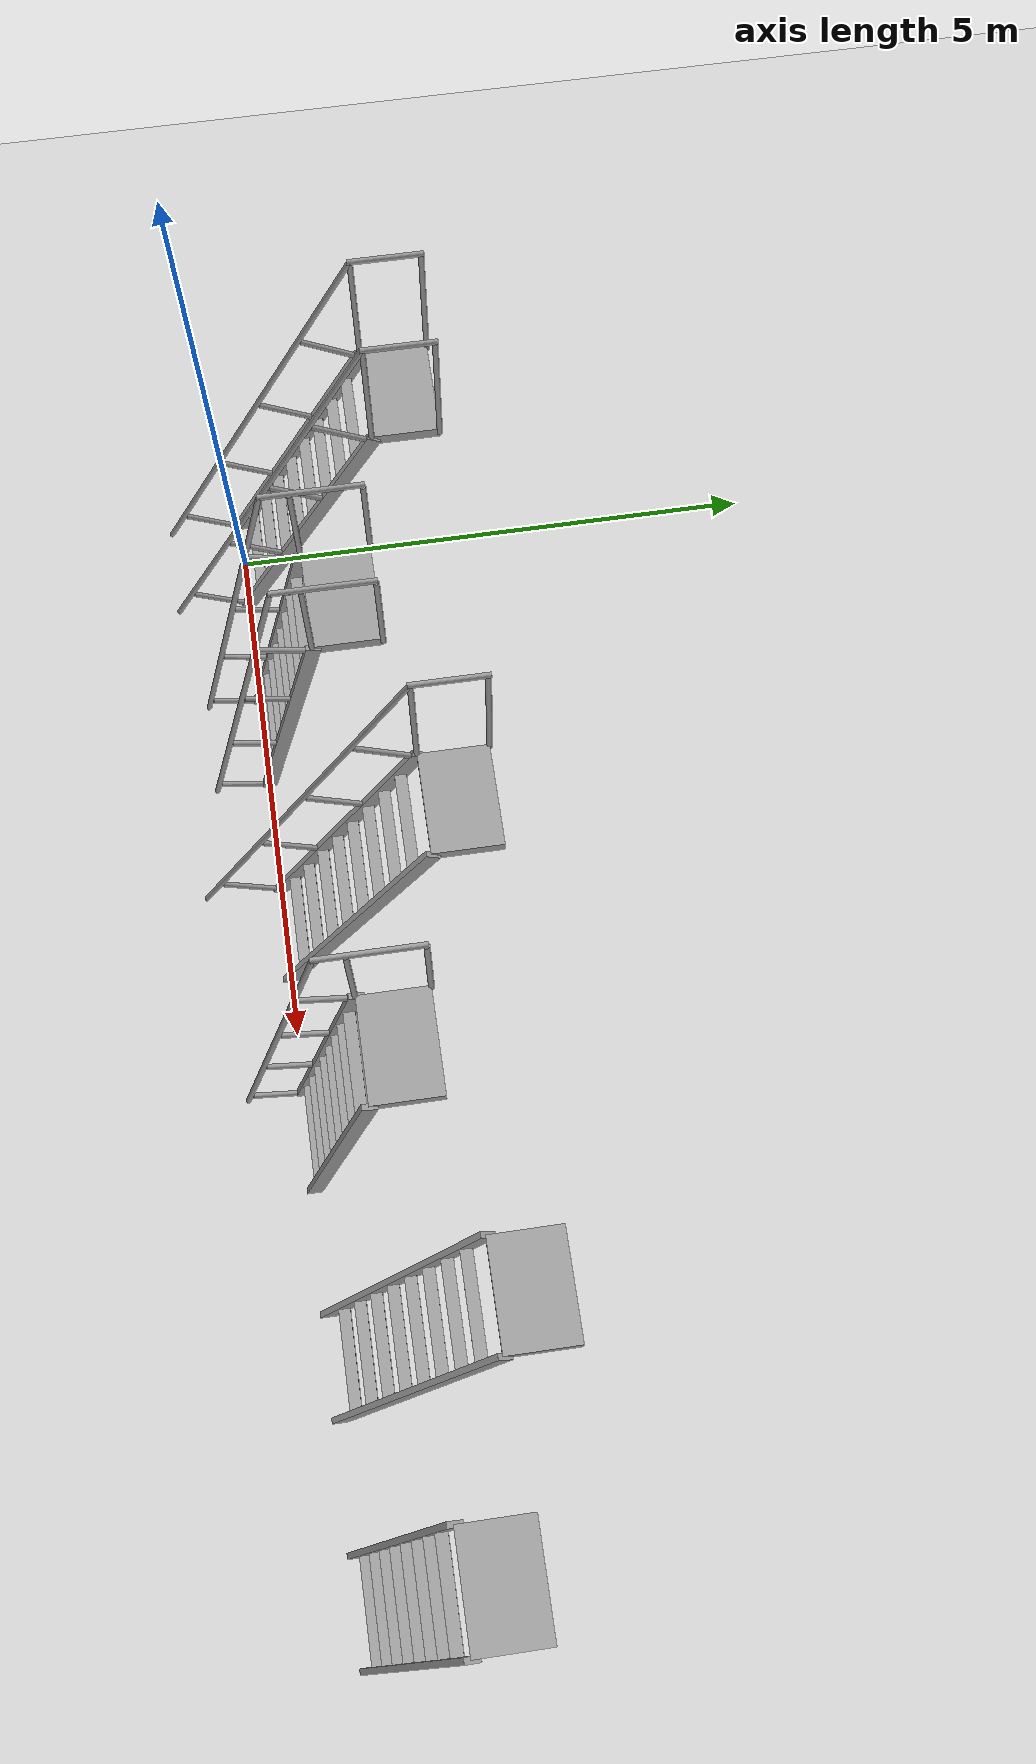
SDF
<?xml version="1.0" ?>
<sdf version="1.4">
  <world name="trials_task_3">
    <physics type="ode">
      <gravity>0 0 -9.81</gravity>
      <ode>
        <solver>
          <type>quick</type>
          <iters>50</iters>
          <sor>1.4</sor>
        </solver>
        <constraints>
          <cfm>0.0</cfm>
          <erp>0.2</erp>
          <contact_max_correcting_vel>100.0</contact_max_correcting_vel>
          <contact_surface_layer>0.0</contact_surface_layer>
        </constraints>
      </ode>
      <real_time_update_rate>1000</real_time_update_rate>
      <max_step_size>0.001</max_step_size>
    </physics>

    <!--A global light source -->
    <include>
      <uri>model://sun</uri>
    </include>

    <!-- A ground plane -->
    <include>
      <uri>model://ground_plane</uri>
    </include>

    <include>
      <name>ladder</name>
      <uri>model://ladder_60deg_2rails</uri>
    </include>

    <include>
      <name>ladder</name>
      <uri>model://ladder_75deg_2rails</uri>
      <pose>2 0 0 0 0 0</pose>
    </include>

    <include>
      <name>ladder</name>
      <uri>model://ladder_60deg_1rails</uri>
      <pose>4 0 0 0 0 0</pose>
    </include>

    <include>
      <name>ladder</name>
      <uri>model://ladder_75deg_1rails</uri>
      <pose>6 0 0 0 0 0</pose>
    </include>

    <include>
      <name>ladder</name>
      <uri>model://ladder_60deg_0rails</uri>
      <pose>8 0 0 0 0 0</pose>
    </include>

    <include>
      <name>ladder</name>
      <uri>model://ladder_75deg_0rails</uri>
      <pose>10 0 0 0 0 0</pose>
    </include>

    <plugin filename="libVRCPlugin.so" name="vrc_plugin">
      <atlas>
        <model_name>atlas</model_name>
        <pin_link>utorso</pin_link>
      </atlas>
      <drc_vehicle>
        <model_name>drc_vehicle_xp900</model_name>
        <seat_link>polaris_ranger_xp900::chassis</seat_link>
      </drc_vehicle>
      <drc_fire_hose>
        <fire_hose_model>fire_hose</fire_hose_model>
        <coupling_link>coupling</coupling_link>
        <standpipe_model>standpipe</standpipe_model>
        <spout_link>standpipe</spout_link>
        <thread_pitch>-1000</thread_pitch>
        <coupling_relative_pose>1.17038e-05 -0.125623 0.35 -0.0412152 -1.57078 1.61199</coupling_relative_pose>
      </drc_fire_hose>
    </plugin>

  </world>
</sdf>

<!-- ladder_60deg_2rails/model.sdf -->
<sdf version="1.5">

  <model name= "ladder_60deg_2rails" >
    <static>true</static>
         <link name="step0" >
           <pose>0 0.15396007178390025 0.26666666666666666 0 0 0 </pose>
           <inertial>
             <mass> 9.7548192</mass>
             <inertia>
             <ixx> 0.009571241631672</ixx>
             <iyy> 0.6596303120915761</iyy>
             <izz> 0.666841521540096</izz>
             <ixy>0</ixy>
             <ixz>0</ixz>
             <iyz>0</iyz>
             </inertia>
           </inertial>

           <collision name="collision">
             <geometry>
              <box>
                <size>  0.9  0.1016  0.0381  </size>
              </box>
             </geometry>
           </collision>

          <visual name="visual">
            <geometry>
              <box>
                <size>  0.9  0.1016  0.0381  </size>
              </box>
            </geometry>
            <material>
              <script>
                <uri>file://media/materials/scripts/gazebo.material</uri>
                <name>Gazebo/Grey</name>
              </script>
            </material>
          </visual>
        </link>
         <link name="step1" >
           <pose>0 0.3079201435678005 0.5333333333333333 0 0 0 </pose>
           <inertial>
             <mass> 9.7548192</mass>
             <inertia>
             <ixx> 0.009571241631672</ixx>
             <iyy> 0.6596303120915761</iyy>
             <izz> 0.666841521540096</izz>
             <ixy>0</ixy>
             <ixz>0</ixz>
             <iyz>0</iyz>
             </inertia>
           </inertial>

           <collision name="collision">
             <geometry>
              <box>
                <size>  0.9  0.1016  0.0381  </size>
              </box>
             </geometry>
           </collision>

          <visual name="visual">
            <geometry>
              <box>
                <size>  0.9  0.1016  0.0381  </size>
              </box>
            </geometry>
            <material>
              <script>
                <uri>file://media/materials/scripts/gazebo.material</uri>
                <name>Gazebo/Grey</name>
              </script>
            </material>
          </visual>
        </link>
         <link name="step2" >
           <pose>0 0.46188021535170076 0.8 0 0 0 </pose>
           <inertial>
             <mass> 9.7548192</mass>
             <inertia>
             <ixx> 0.009571241631672</ixx>
             <iyy> 0.6596303120915761</iyy>
             <izz> 0.666841521540096</izz>
             <ixy>0</ixy>
             <ixz>0</ixz>
             <iyz>0</iyz>
             </inertia>
           </inertial>

           <collision name="collision">
             <geometry>
              <box>
                <size>  0.9  0.1016  0.0381  </size>
              </box>
             </geometry>
           </collision>

          <visual name="visual">
            <geometry>
              <box>
                <size>  0.9  0.1016  0.0381  </size>
              </box>
            </geometry>
            <material>
              <script>
                <uri>file://media/materials/scripts/gazebo.material</uri>
                <name>Gazebo/Grey</name>
              </script>
            </material>
          </visual>
        </link>
         <link name="step3" >
           <pose>0 0.615840287135601 1.0666666666666667 0 0 0 </pose>
           <inertial>
             <mass> 9.7548192</mass>
             <inertia>
             <ixx> 0.009571241631672</ixx>
             <iyy> 0.6596303120915761</iyy>
             <izz> 0.666841521540096</izz>
             <ixy>0</ixy>
             <ixz>0</ixz>
             <iyz>0</iyz>
             </inertia>
           </inertial>

           <collision name="collision">
             <geometry>
              <box>
                <size>  0.9  0.1016  0.0381  </size>
              </box>
             </geometry>
           </collision>

          <visual name="visual">
            <geometry>
              <box>
                <size>  0.9  0.1016  0.0381  </size>
              </box>
            </geometry>
            <material>
              <script>
                <uri>file://media/materials/scripts/gazebo.material</uri>
                <name>Gazebo/Grey</name>
              </script>
            </material>
          </visual>
        </link>
         <link name="step4" >
           <pose>0 0.7698003589195013 1.3333333333333333 0 0 0 </pose>
           <inertial>
             <mass> 9.7548192</mass>
             <inertia>
             <ixx> 0.009571241631672</ixx>
             <iyy> 0.6596303120915761</iyy>
             <izz> 0.666841521540096</izz>
             <ixy>0</ixy>
             <ixz>0</ixz>
             <iyz>0</iyz>
             </inertia>
           </inertial>

           <collision name="collision">
             <geometry>
              <box>
                <size>  0.9  0.1016  0.0381  </size>
              </box>
             </geometry>
           </collision>

          <visual name="visual">
            <geometry>
              <box>
                <size>  0.9  0.1016  0.0381  </size>
              </box>
            </geometry>
            <material>
              <script>
                <uri>file://media/materials/scripts/gazebo.material</uri>
                <name>Gazebo/Grey</name>
              </script>
            </material>
          </visual>
        </link>
         <link name="step5" >
           <pose>0 0.9237604307034015 1.6 0 0 0 </pose>
           <inertial>
             <mass> 9.7548192</mass>
             <inertia>
             <ixx> 0.009571241631672</ixx>
             <iyy> 0.6596303120915761</iyy>
             <izz> 0.666841521540096</izz>
             <ixy>0</ixy>
             <ixz>0</ixz>
             <iyz>0</iyz>
             </inertia>
           </inertial>

           <collision name="collision">
             <geometry>
              <box>
                <size>  0.9  0.1016  0.0381  </size>
              </box>
             </geometry>
           </collision>

          <visual name="visual">
            <geometry>
              <box>
                <size>  0.9  0.1016  0.0381  </size>
              </box>
            </geometry>
            <material>
              <script>
                <uri>file://media/materials/scripts/gazebo.material</uri>
                <name>Gazebo/Grey</name>
              </script>
            </material>
          </visual>
        </link>
         <link name="step6" >
           <pose>0 1.0777205024873018 1.8666666666666667 0 0 0 </pose>
           <inertial>
             <mass> 9.7548192</mass>
             <inertia>
             <ixx> 0.009571241631672</ixx>
             <iyy> 0.6596303120915761</iyy>
             <izz> 0.666841521540096</izz>
             <ixy>0</ixy>
             <ixz>0</ixz>
             <iyz>0</iyz>
             </inertia>
           </inertial>

           <collision name="collision">
             <geometry>
              <box>
                <size>  0.9  0.1016  0.0381  </size>
              </box>
             </geometry>
           </collision>

          <visual name="visual">
            <geometry>
              <box>
                <size>  0.9  0.1016  0.0381  </size>
              </box>
            </geometry>
            <material>
              <script>
                <uri>file://media/materials/scripts/gazebo.material</uri>
                <name>Gazebo/Grey</name>
              </script>
            </material>
          </visual>
        </link>
         <link name="step7" >
           <pose>0 1.231680574271202 2.1333333333333333 0 0 0 </pose>
           <inertial>
             <mass> 9.7548192</mass>
             <inertia>
             <ixx> 0.009571241631672</ixx>
             <iyy> 0.6596303120915761</iyy>
             <izz> 0.666841521540096</izz>
             <ixy>0</ixy>
             <ixz>0</ixz>
             <iyz>0</iyz>
             </inertia>
           </inertial>

           <collision name="collision">
             <geometry>
              <box>
                <size>  0.9  0.1016  0.0381  </size>
              </box>
             </geometry>
           </collision>

          <visual name="visual">
            <geometry>
              <box>
                <size>  0.9  0.1016  0.0381  </size>
              </box>
            </geometry>
            <material>
              <script>
                <uri>file://media/materials/scripts/gazebo.material</uri>
                <name>Gazebo/Grey</name>
              </script>
            </material>
          </visual>
        </link>
    <link name="landing">
      <pose>0 1.6856406460551023 2.4 0 0 0 </pose>
        <inertial>
          <mass> 57.607200000000006</mass>
          <inertia>
          <ixx> 1.735184598966</ixx>
          <iyy> 3.8954545989660008</iyy>
          <izz> 5.616702</izz>
          <ixy>0</ixy>
          <ixz>0</ixz>
          <iyz>0</iyz>
          </inertia>
        </inertial>

        <collision name="collision">
          <geometry>
           <box>
             <size> 0.9 0.6 0.1016</size>
           </box>
          </geometry>
        </collision>

        <visual name="visual">
          <geometry>
            <box>
             <size> 0.9 0.6 0.1016</size>
            </box>
          </geometry>
          <material>
            <script>
              <uri>file://media/materials/scripts/gazebo.material</uri>
              <name>Gazebo/Grey</name>
            </script>
          </material>
        </visual>
    </link>

      <link name="left_side_wall" >
        <pose>-0.45 0.6928203230275511 1.2 1.0471975511965976 0 0 </pose>
        <collision name="collision">
          <geometry>
            <box>
              <size> 0.0508  2.851281292110204  0.13 </size>
            </box>
          </geometry>
        </collision>

        <visual name="visual">
          <geometry>
            <box>
              <size> 0.0508  2.851281292110204  0.13 </size>
            </box>
          </geometry>
          <material>
            <script>
              <uri>file://media/materials/scripts/gazebo.material</uri>
              <name>Gazebo/Grey</name>
            </script>
          </material>
        </visual>

      </link>
      <link name="right_side_wall" >
        <pose>0.45 0.6928203230275511 1.2 1.0471975511965976 0 0 </pose>
        <collision name="collision">
          <geometry>
            <box>
              <size> 0.0508  2.851281292110204  0.13 </size>
            </box>
          </geometry>
        </collision>

        <visual name="visual">
          <geometry>
            <box>
              <size> 0.0508  2.851281292110204  0.13 </size>
            </box>
          </geometry>
          <material>
            <script>
              <uri>file://media/materials/scripts/gazebo.material</uri>
              <name>Gazebo/Grey</name>
            </script>
          </material>
        </visual>

      </link>
         <link name="left_railing_long" >
           <pose>-0.45 0.34282032302755117 1.8062177826491068 -0.5235987755982989 0 0 </pose>

            <collision name="collision">
              <geometry>
                <cylinder>
                  <radius>0.02413</radius>
                  <length>4.171281292110204</length>
                </cylinder>
              </geometry>
            </collision>

            <visual name="visual">
              <geometry>
                <cylinder>
                  <radius>0.02413</radius>
                  <length>4.171281292110204</length>
                </cylinder>
              </geometry>
              <material>
                <script>
                  <uri>file://media/materials/scripts/gazebo.material</uri>
                  <name>Gazebo/Grey</name>
                </script>
              </material>
            </visual>
         </link>
              <link name="left_railing_upright0" >
                <pose> -0.45 -0.2749630657015592 0.15875 1.0471975511965976 0 0 </pose>

                <collision name="collision">
                  <geometry>
                    <cylinder>
                      <radius>0.02413</radius>
                      <length>0.5412177826491069</length>
                    </cylinder>
                  </geometry>
                </collision>

                <visual name="visual">
                  <geometry>
                    <cylinder>
                      <radius>0.02413</radius>
                      <length>0.5412177826491069</length>
                    </cylinder>
                  </geometry>
                  <material>
                    <script>
                      <uri>file://media/materials/scripts/gazebo.material</uri>
                      <name>Gazebo/Grey</name>
                    </script>
                  </material>
                </visual>
              </link>
              <link name="left_railing_upright1" >
                <pose> -0.45 0.18691714965014153 0.95875 1.0471975511965976 0 0 </pose>

                <collision name="collision">
                  <geometry>
                    <cylinder>
                      <radius>0.02413</radius>
                      <length>0.5412177826491069</length>
                    </cylinder>
                  </geometry>
                </collision>

                <visual name="visual">
                  <geometry>
                    <cylinder>
                      <radius>0.02413</radius>
                      <length>0.5412177826491069</length>
                    </cylinder>
                  </geometry>
                  <material>
                    <script>
                      <uri>file://media/materials/scripts/gazebo.material</uri>
                      <name>Gazebo/Grey</name>
                    </script>
                  </material>
                </visual>
              </link>
              <link name="left_railing_upright2" >
                <pose> -0.45 0.6487973650018424 1.7587499999999998 1.0471975511965976 0 0 </pose>

                <collision name="collision">
                  <geometry>
                    <cylinder>
                      <radius>0.02413</radius>
                      <length>0.5412177826491069</length>
                    </cylinder>
                  </geometry>
                </collision>

                <visual name="visual">
                  <geometry>
                    <cylinder>
                      <radius>0.02413</radius>
                      <length>0.5412177826491069</length>
                    </cylinder>
                  </geometry>
                  <material>
                    <script>
                      <uri>file://media/materials/scripts/gazebo.material</uri>
                      <name>Gazebo/Grey</name>
                    </script>
                  </material>
                </visual>
              </link>
              <link name="left_railing_upright3" >
                <pose> -0.45 1.1106775803535431 2.55875 1.0471975511965976 0 0 </pose>

                <collision name="collision">
                  <geometry>
                    <cylinder>
                      <radius>0.02413</radius>
                      <length>0.5412177826491069</length>
                    </cylinder>
                  </geometry>
                </collision>

                <visual name="visual">
                  <geometry>
                    <cylinder>
                      <radius>0.02413</radius>
                      <length>0.5412177826491069</length>
                    </cylinder>
                  </geometry>
                  <material>
                    <script>
                      <uri>file://media/materials/scripts/gazebo.material</uri>
                      <name>Gazebo/Grey</name>
                    </script>
                  </material>
                </visual>
              </link>

         <link name="left_railing_landing_top" >

           <pose> -0.45 1.6856406460551023 3.6124355652982136 1.5707963267948966 0 0 </pose>

           <collision name="collision">
             <geometry>
               <cylinder>
                 <radius>0.02413</radius>
                 <length>0.64826</length>
               </cylinder>
             </geometry>
           </collision>

           <visual name="visual">
             <geometry>
               <cylinder>
                 <radius>0.02413</radius>
                 <length>0.64826</length>
               </cylinder>
             </geometry>
             <material>
               <script>
                 <uri>file://media/materials/scripts/gazebo.material</uri>
                 <name>Gazebo/Grey</name>
               </script>
             </material>
           </visual>
         </link>

            <link name="left_railing_landing_upright_0">
              <pose>-0.45 1.3856406460551023 3.0062177826491068 0 0 0</pose>
              <collision name="collision">
                <geometry>
                  <cylinder>
                    <radius>0.02413</radius>
                    <length>1.2124355652982137</length>
                  </cylinder>
                </geometry>
              </collision>

              <visual name="visual">
                <geometry>
                  <cylinder>
                    <radius>0.02413</radius>
                    <length>1.2124355652982137</length>
                  </cylinder>
                </geometry>
                <material>
                  <script>
                    <uri>file://media/materials/scripts/gazebo.material</uri>
                    <name>Gazebo/Grey</name>
                  </script>
                </material>
              </visual>
            </link>
            <link name="left_railing_landing_upright_1">
              <pose>-0.45 1.9856406460551024 3.0062177826491068 0 0 0</pose>
              <collision name="collision">
                <geometry>
                  <cylinder>
                    <radius>0.02413</radius>
                    <length>1.2124355652982137</length>
                  </cylinder>
                </geometry>
              </collision>

              <visual name="visual">
                <geometry>
                  <cylinder>
                    <radius>0.02413</radius>
                    <length>1.2124355652982137</length>
                  </cylinder>
                </geometry>
                <material>
                  <script>
                    <uri>file://media/materials/scripts/gazebo.material</uri>
                    <name>Gazebo/Grey</name>
                  </script>
                </material>
              </visual>
            </link>

         <link name="right_railing_long" >
           <pose>0.45 0.34282032302755117 1.8062177826491068 -0.5235987755982989 0 0 </pose>

            <collision name="collision">
              <geometry>
                <cylinder>
                  <radius>0.02413</radius>
                  <length>4.171281292110204</length>
                </cylinder>
              </geometry>
            </collision>

            <visual name="visual">
              <geometry>
                <cylinder>
                  <radius>0.02413</radius>
                  <length>4.171281292110204</length>
                </cylinder>
              </geometry>
              <material>
                <script>
                  <uri>file://media/materials/scripts/gazebo.material</uri>
                  <name>Gazebo/Grey</name>
                </script>
              </material>
            </visual>
         </link>
              <link name="right_railing_upright0" >
                <pose> 0.45 -0.2749630657015592 0.15875 1.0471975511965976 0 0 </pose>

                <collision name="collision">
                  <geometry>
                    <cylinder>
                      <radius>0.02413</radius>
                      <length>0.5412177826491069</length>
                    </cylinder>
                  </geometry>
                </collision>

                <visual name="visual">
                  <geometry>
                    <cylinder>
                      <radius>0.02413</radius>
                      <length>0.5412177826491069</length>
                    </cylinder>
                  </geometry>
                  <material>
                    <script>
                      <uri>file://media/materials/scripts/gazebo.material</uri>
                      <name>Gazebo/Grey</name>
                    </script>
                  </material>
                </visual>
              </link>
              <link name="right_railing_upright1" >
                <pose> 0.45 0.18691714965014153 0.95875 1.0471975511965976 0 0 </pose>

                <collision name="collision">
                  <geometry>
                    <cylinder>
                      <radius>0.02413</radius>
                      <length>0.5412177826491069</length>
                    </cylinder>
                  </geometry>
                </collision>

                <visual name="visual">
                  <geometry>
                    <cylinder>
                      <radius>0.02413</radius>
                      <length>0.5412177826491069</length>
                    </cylinder>
                  </geometry>
                  <material>
                    <script>
                      <uri>file://media/materials/scripts/gazebo.material</uri>
                      <name>Gazebo/Grey</name>
                    </script>
                  </material>
                </visual>
              </link>
              <link name="right_railing_upright2" >
                <pose> 0.45 0.6487973650018424 1.7587499999999998 1.0471975511965976 0 0 </pose>

                <collision name="collision">
                  <geometry>
                    <cylinder>
                      <radius>0.02413</radius>
                      <length>0.5412177826491069</length>
                    </cylinder>
                  </geometry>
                </collision>

                <visual name="visual">
                  <geometry>
                    <cylinder>
                      <radius>0.02413</radius>
                      <length>0.5412177826491069</length>
                    </cylinder>
                  </geometry>
                  <material>
                    <script>
                      <uri>file://media/materials/scripts/gazebo.material</uri>
                      <name>Gazebo/Grey</name>
                    </script>
                  </material>
                </visual>
              </link>
              <link name="right_railing_upright3" >
                <pose> 0.45 1.1106775803535431 2.55875 1.0471975511965976 0 0 </pose>

                <collision name="collision">
                  <geometry>
                    <cylinder>
                      <radius>0.02413</radius>
                      <length>0.5412177826491069</length>
                    </cylinder>
                  </geometry>
                </collision>

                <visual name="visual">
                  <geometry>
                    <cylinder>
                      <radius>0.02413</radius>
                      <length>0.5412177826491069</length>
                    </cylinder>
                  </geometry>
                  <material>
                    <script>
                      <uri>file://media/materials/scripts/gazebo.material</uri>
                      <name>Gazebo/Grey</name>
                    </script>
                  </material>
                </visual>
              </link>

         <link name="right_railing_landing_top" >

           <pose> 0.45 1.6856406460551023 3.6124355652982136 1.5707963267948966 0 0 </pose>

           <collision name="collision">
             <geometry>
               <cylinder>
                 <radius>0.02413</radius>
                 <length>0.64826</length>
               </cylinder>
             </geometry>
           </collision>

           <visual name="visual">
             <geometry>
               <cylinder>
                 <radius>0.02413</radius>
                 <length>0.64826</length>
               </cylinder>
             </geometry>
             <material>
               <script>
                 <uri>file://media/materials/scripts/gazebo.material</uri>
                 <name>Gazebo/Grey</name>
               </script>
             </material>
           </visual>
         </link>

            <link name="right_railing_landing_upright_0">
              <pose>0.45 1.3856406460551023 3.0062177826491068 0 0 0</pose>
              <collision name="collision">
                <geometry>
                  <cylinder>
                    <radius>0.02413</radius>
                    <length>1.2124355652982137</length>
                  </cylinder>
                </geometry>
              </collision>

              <visual name="visual">
                <geometry>
                  <cylinder>
                    <radius>0.02413</radius>
                    <length>1.2124355652982137</length>
                  </cylinder>
                </geometry>
                <material>
                  <script>
                    <uri>file://media/materials/scripts/gazebo.material</uri>
                    <name>Gazebo/Grey</name>
                  </script>
                </material>
              </visual>
            </link>
            <link name="right_railing_landing_upright_1">
              <pose>0.45 1.9856406460551024 3.0062177826491068 0 0 0</pose>
              <collision name="collision">
                <geometry>
                  <cylinder>
                    <radius>0.02413</radius>
                    <length>1.2124355652982137</length>
                  </cylinder>
                </geometry>
              </collision>

              <visual name="visual">
                <geometry>
                  <cylinder>
                    <radius>0.02413</radius>
                    <length>1.2124355652982137</length>
                  </cylinder>
                </geometry>
                <material>
                  <script>
                    <uri>file://media/materials/scripts/gazebo.material</uri>
                    <name>Gazebo/Grey</name>
                  </script>
                </material>
              </visual>
            </link>

  </model>
</sdf>

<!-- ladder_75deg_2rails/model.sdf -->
<sdf version="1.5">

  <model name= "ladder_75deg_2rails" >
    <static>true</static>
         <link name="step0" >
           <pose>0 0.07145311798163272 0.26666666666666666 0 0 0 </pose>
           <inertial>
             <mass> 9.7548192</mass>
             <inertia>
             <ixx> 0.009571241631672</ixx>
             <iyy> 0.6596303120915761</iyy>
             <izz> 0.666841521540096</izz>
             <ixy>0</ixy>
             <ixz>0</ixz>
             <iyz>0</iyz>
             </inertia>
           </inertial>

           <collision name="collision">
             <geometry>
              <box>
                <size>  0.9  0.1016  0.0381  </size>
              </box>
             </geometry>
           </collision>

          <visual name="visual">
            <geometry>
              <box>
                <size>  0.9  0.1016  0.0381  </size>
              </box>
            </geometry>
            <material>
              <script>
                <uri>file://media/materials/scripts/gazebo.material</uri>
                <name>Gazebo/Grey</name>
              </script>
            </material>
          </visual>
        </link>
         <link name="step1" >
           <pose>0 0.14290623596326543 0.5333333333333333 0 0 0 </pose>
           <inertial>
             <mass> 9.7548192</mass>
             <inertia>
             <ixx> 0.009571241631672</ixx>
             <iyy> 0.6596303120915761</iyy>
             <izz> 0.666841521540096</izz>
             <ixy>0</ixy>
             <ixz>0</ixz>
             <iyz>0</iyz>
             </inertia>
           </inertial>

           <collision name="collision">
             <geometry>
              <box>
                <size>  0.9  0.1016  0.0381  </size>
              </box>
             </geometry>
           </collision>

          <visual name="visual">
            <geometry>
              <box>
                <size>  0.9  0.1016  0.0381  </size>
              </box>
            </geometry>
            <material>
              <script>
                <uri>file://media/materials/scripts/gazebo.material</uri>
                <name>Gazebo/Grey</name>
              </script>
            </material>
          </visual>
        </link>
         <link name="step2" >
           <pose>0 0.21435935394489813 0.8 0 0 0 </pose>
           <inertial>
             <mass> 9.7548192</mass>
             <inertia>
             <ixx> 0.009571241631672</ixx>
             <iyy> 0.6596303120915761</iyy>
             <izz> 0.666841521540096</izz>
             <ixy>0</ixy>
             <ixz>0</ixz>
             <iyz>0</iyz>
             </inertia>
           </inertial>

           <collision name="collision">
             <geometry>
              <box>
                <size>  0.9  0.1016  0.0381  </size>
              </box>
             </geometry>
           </collision>

          <visual name="visual">
            <geometry>
              <box>
                <size>  0.9  0.1016  0.0381  </size>
              </box>
            </geometry>
            <material>
              <script>
                <uri>file://media/materials/scripts/gazebo.material</uri>
                <name>Gazebo/Grey</name>
              </script>
            </material>
          </visual>
        </link>
         <link name="step3" >
           <pose>0 0.28581247192653086 1.0666666666666667 0 0 0 </pose>
           <inertial>
             <mass> 9.7548192</mass>
             <inertia>
             <ixx> 0.009571241631672</ixx>
             <iyy> 0.6596303120915761</iyy>
             <izz> 0.666841521540096</izz>
             <ixy>0</ixy>
             <ixz>0</ixz>
             <iyz>0</iyz>
             </inertia>
           </inertial>

           <collision name="collision">
             <geometry>
              <box>
                <size>  0.9  0.1016  0.0381  </size>
              </box>
             </geometry>
           </collision>

          <visual name="visual">
            <geometry>
              <box>
                <size>  0.9  0.1016  0.0381  </size>
              </box>
            </geometry>
            <material>
              <script>
                <uri>file://media/materials/scripts/gazebo.material</uri>
                <name>Gazebo/Grey</name>
              </script>
            </material>
          </visual>
        </link>
         <link name="step4" >
           <pose>0 0.3572655899081636 1.3333333333333333 0 0 0 </pose>
           <inertial>
             <mass> 9.7548192</mass>
             <inertia>
             <ixx> 0.009571241631672</ixx>
             <iyy> 0.6596303120915761</iyy>
             <izz> 0.666841521540096</izz>
             <ixy>0</ixy>
             <ixz>0</ixz>
             <iyz>0</iyz>
             </inertia>
           </inertial>

           <collision name="collision">
             <geometry>
              <box>
                <size>  0.9  0.1016  0.0381  </size>
              </box>
             </geometry>
           </collision>

          <visual name="visual">
            <geometry>
              <box>
                <size>  0.9  0.1016  0.0381  </size>
              </box>
            </geometry>
            <material>
              <script>
                <uri>file://media/materials/scripts/gazebo.material</uri>
                <name>Gazebo/Grey</name>
              </script>
            </material>
          </visual>
        </link>
         <link name="step5" >
           <pose>0 0.42871870788979627 1.6 0 0 0 </pose>
           <inertial>
             <mass> 9.7548192</mass>
             <inertia>
             <ixx> 0.009571241631672</ixx>
             <iyy> 0.6596303120915761</iyy>
             <izz> 0.666841521540096</izz>
             <ixy>0</ixy>
             <ixz>0</ixz>
             <iyz>0</iyz>
             </inertia>
           </inertial>

           <collision name="collision">
             <geometry>
              <box>
                <size>  0.9  0.1016  0.0381  </size>
              </box>
             </geometry>
           </collision>

          <visual name="visual">
            <geometry>
              <box>
                <size>  0.9  0.1016  0.0381  </size>
              </box>
            </geometry>
            <material>
              <script>
                <uri>file://media/materials/scripts/gazebo.material</uri>
                <name>Gazebo/Grey</name>
              </script>
            </material>
          </visual>
        </link>
         <link name="step6" >
           <pose>0 0.500171825871429 1.8666666666666667 0 0 0 </pose>
           <inertial>
             <mass> 9.7548192</mass>
             <inertia>
             <ixx> 0.009571241631672</ixx>
             <iyy> 0.6596303120915761</iyy>
             <izz> 0.666841521540096</izz>
             <ixy>0</ixy>
             <ixz>0</ixz>
             <iyz>0</iyz>
             </inertia>
           </inertial>

           <collision name="collision">
             <geometry>
              <box>
                <size>  0.9  0.1016  0.0381  </size>
              </box>
             </geometry>
           </collision>

          <visual name="visual">
            <geometry>
              <box>
                <size>  0.9  0.1016  0.0381  </size>
              </box>
            </geometry>
            <material>
              <script>
                <uri>file://media/materials/scripts/gazebo.material</uri>
                <name>Gazebo/Grey</name>
              </script>
            </material>
          </visual>
        </link>
         <link name="step7" >
           <pose>0 0.5716249438530617 2.1333333333333333 0 0 0 </pose>
           <inertial>
             <mass> 9.7548192</mass>
             <inertia>
             <ixx> 0.009571241631672</ixx>
             <iyy> 0.6596303120915761</iyy>
             <izz> 0.666841521540096</izz>
             <ixy>0</ixy>
             <ixz>0</ixz>
             <iyz>0</iyz>
             </inertia>
           </inertial>

           <collision name="collision">
             <geometry>
              <box>
                <size>  0.9  0.1016  0.0381  </size>
              </box>
             </geometry>
           </collision>

          <visual name="visual">
            <geometry>
              <box>
                <size>  0.9  0.1016  0.0381  </size>
              </box>
            </geometry>
            <material>
              <script>
                <uri>file://media/materials/scripts/gazebo.material</uri>
                <name>Gazebo/Grey</name>
              </script>
            </material>
          </visual>
        </link>
    <link name="landing">
      <pose>0 0.9430780618346943 2.4 0 0 0 </pose>
        <inertial>
          <mass> 57.607200000000006</mass>
          <inertia>
          <ixx> 1.735184598966</ixx>
          <iyy> 3.8954545989660008</iyy>
          <izz> 5.616702</izz>
          <ixy>0</ixy>
          <ixz>0</ixz>
          <iyz>0</iyz>
          </inertia>
        </inertial>

        <collision name="collision">
          <geometry>
           <box>
             <size> 0.9 0.6 0.1016</size>
           </box>
          </geometry>
        </collision>

        <visual name="visual">
          <geometry>
            <box>
             <size> 0.9 0.6 0.1016</size>
            </box>
          </geometry>
          <material>
            <script>
              <uri>file://media/materials/scripts/gazebo.material</uri>
              <name>Gazebo/Grey</name>
            </script>
          </material>
        </visual>
    </link>

      <link name="left_side_wall" >
        <pose>-0.45 0.3215390309173472 1.2 1.3089969389957472 0 0 </pose>
        <collision name="collision">
          <geometry>
            <box>
              <size> 0.0508  2.564662832984199  0.13 </size>
            </box>
          </geometry>
        </collision>

        <visual name="visual">
          <geometry>
            <box>
              <size> 0.0508  2.564662832984199  0.13 </size>
            </box>
          </geometry>
          <material>
            <script>
              <uri>file://media/materials/scripts/gazebo.material</uri>
              <name>Gazebo/Grey</name>
            </script>
          </material>
        </visual>

      </link>
      <link name="right_side_wall" >
        <pose>0.45 0.3215390309173472 1.2 1.3089969389957472 0 0 </pose>
        <collision name="collision">
          <geometry>
            <box>
              <size> 0.0508  2.564662832984199  0.13 </size>
            </box>
          </geometry>
        </collision>

        <visual name="visual">
          <geometry>
            <box>
              <size> 0.0508  2.564662832984199  0.13 </size>
            </box>
          </geometry>
          <material>
            <script>
              <uri>file://media/materials/scripts/gazebo.material</uri>
              <name>Gazebo/Grey</name>
            </script>
          </material>
        </visual>

      </link>

         <link name="left_railing_long" >
           <pose>-0.45 -0.0534609690826528 1.6665063509461095 -0.26179938779914935 0 0 </pose>

            <collision name="collision">
              <geometry>
                <cylinder>
                  <radius>0.02413</radius>
                  <length>3.5152934205488977</length>
                </cylinder>
              </geometry>
            </collision>

            <visual name="visual">
              <geometry>
                <cylinder>
                  <radius>0.02413</radius>
                  <length>3.5152934205488977</length>
                </cylinder>
              </geometry>
              <material>
                <script>
                  <uri>file://media/materials/scripts/gazebo.material</uri>
                  <name>Gazebo/Grey</name>
                </script>
              </material>
            </visual>
         </link>

              <link name="left_railing_upright0" >
                <pose> -0.45 -0.21008886721787234 0.05629314230979826 1.3089969389957472 0 0 </pose>

                <collision name="collision">
                  <geometry>
                    <cylinder>
                      <radius>0.02413</radius>
                      <length>0.48296291314453416</length>
                    </cylinder>
                  </geometry>
                </collision>

                <visual name="visual">
                  <geometry>
                    <cylinder>
                      <radius>0.02413</radius>
                      <length>0.48296291314453416</length>
                    </cylinder>
                  </geometry>
                  <material>
                    <script>
                      <uri>file://media/materials/scripts/gazebo.material</uri>
                      <name>Gazebo/Grey</name>
                    </script>
                  </material>
                </visual>
              </link>
              <link name="left_railing_upright1" >
                <pose> -0.45 0.004270486727025777 0.8562931423097981 1.3089969389957472 0 0 </pose>

                <collision name="collision">
                  <geometry>
                    <cylinder>
                      <radius>0.02413</radius>
                      <length>0.48296291314453416</length>
                    </cylinder>
                  </geometry>
                </collision>

                <visual name="visual">
                  <geometry>
                    <cylinder>
                      <radius>0.02413</radius>
                      <length>0.48296291314453416</length>
                    </cylinder>
                  </geometry>
                  <material>
                    <script>
                      <uri>file://media/materials/scripts/gazebo.material</uri>
                      <name>Gazebo/Grey</name>
                    </script>
                  </material>
                </visual>
              </link>
              <link name="left_railing_upright2" >
                <pose> -0.45 0.21862984067192393 1.6562931423097982 1.3089969389957472 0 0 </pose>

                <collision name="collision">
                  <geometry>
                    <cylinder>
                      <radius>0.02413</radius>
                      <length>0.48296291314453416</length>
                    </cylinder>
                  </geometry>
                </collision>

                <visual name="visual">
                  <geometry>
                    <cylinder>
                      <radius>0.02413</radius>
                      <length>0.48296291314453416</length>
                    </cylinder>
                  </geometry>
                  <material>
                    <script>
                      <uri>file://media/materials/scripts/gazebo.material</uri>
                      <name>Gazebo/Grey</name>
                    </script>
                  </material>
                </visual>
              </link>
              <link name="left_railing_upright3" >
                <pose> -0.45 0.43298919461682206 2.4562931423097982 1.3089969389957472 0 0 </pose>

                <collision name="collision">
                  <geometry>
                    <cylinder>
                      <radius>0.02413</radius>
                      <length>0.48296291314453416</length>
                    </cylinder>
                  </geometry>
                </collision>

                <visual name="visual">
                  <geometry>
                    <cylinder>
                      <radius>0.02413</radius>
                      <length>0.48296291314453416</length>
                    </cylinder>
                  </geometry>
                  <material>
                    <script>
                      <uri>file://media/materials/scripts/gazebo.material</uri>
                      <name>Gazebo/Grey</name>
                    </script>
                  </material>
                </visual>
              </link>

         <link name="left_railing_landing_top" >

           <pose> -0.45 0.8180780618346943 3.357142701892219 1.5707963267948966 0 0 </pose>

           <collision name="collision">
             <geometry>
               <cylinder>
                 <radius>0.02413</radius>
                 <length>0.87413</length>
               </cylinder>
             </geometry>
           </collision>

           <visual name="visual">
             <geometry>
               <cylinder>
                 <radius>0.02413</radius>
                 <length>0.87413</length>
               </cylinder>
             </geometry>
             <material>
               <script>
                 <uri>file://media/materials/scripts/gazebo.material</uri>
                 <name>Gazebo/Grey</name>
               </script>
             </material>
           </visual>
         </link>

            <link name="left_railing_landing_upright_0">
              <pose>-0.45 0.6430780618346944 2.8665063509461097 0 0 0</pose>
              <collision name="collision">
                <geometry>
                  <cylinder>
                    <radius>0.02413</radius>
                    <length>0.9330127018922194</length>
                  </cylinder>
                </geometry>
              </collision>

              <visual name="visual">
                <geometry>
                  <cylinder>
                    <radius>0.02413</radius>
                    <length>0.9330127018922194</length>
                  </cylinder>
                </geometry>
                <material>
                  <script>
                    <uri>file://media/materials/scripts/gazebo.material</uri>
                    <name>Gazebo/Grey</name>
                  </script>
                </material>
              </visual>
            </link>
            <link name="left_railing_landing_upright_1">
              <pose>-0.45 1.2430780618346944 2.8665063509461097 0 0 0</pose>
              <collision name="collision">
                <geometry>
                  <cylinder>
                    <radius>0.02413</radius>
                    <length>0.9330127018922194</length>
                  </cylinder>
                </geometry>
              </collision>

              <visual name="visual">
                <geometry>
                  <cylinder>
                    <radius>0.02413</radius>
                    <length>0.9330127018922194</length>
                  </cylinder>
                </geometry>
                <material>
                  <script>
                    <uri>file://media/materials/scripts/gazebo.material</uri>
                    <name>Gazebo/Grey</name>
                  </script>
                </material>
              </visual>
            </link>

         <link name="right_railing_long" >
           <pose>0.45 -0.0534609690826528 1.6665063509461095 -0.26179938779914935 0 0 </pose>

            <collision name="collision">
              <geometry>
                <cylinder>
                  <radius>0.02413</radius>
                  <length>3.5152934205488977</length>
                </cylinder>
              </geometry>
            </collision>

            <visual name="visual">
              <geometry>
                <cylinder>
                  <radius>0.02413</radius>
                  <length>3.5152934205488977</length>
                </cylinder>
              </geometry>
              <material>
                <script>
                  <uri>file://media/materials/scripts/gazebo.material</uri>
                  <name>Gazebo/Grey</name>
                </script>
              </material>
            </visual>
         </link>

              <link name="right_railing_upright0" >
                <pose> 0.45 -0.21008886721787234 0.05629314230979826 1.3089969389957472 0 0 </pose>

                <collision name="collision">
                  <geometry>
                    <cylinder>
                      <radius>0.02413</radius>
                      <length>0.48296291314453416</length>
                    </cylinder>
                  </geometry>
                </collision>

                <visual name="visual">
                  <geometry>
                    <cylinder>
                      <radius>0.02413</radius>
                      <length>0.48296291314453416</length>
                    </cylinder>
                  </geometry>
                  <material>
                    <script>
                      <uri>file://media/materials/scripts/gazebo.material</uri>
                      <name>Gazebo/Grey</name>
                    </script>
                  </material>
                </visual>
              </link>
              <link name="right_railing_upright1" >
                <pose> 0.45 0.004270486727025777 0.8562931423097981 1.3089969389957472 0 0 </pose>

                <collision name="collision">
                  <geometry>
                    <cylinder>
                      <radius>0.02413</radius>
                      <length>0.48296291314453416</length>
                    </cylinder>
                  </geometry>
                </collision>

                <visual name="visual">
                  <geometry>
                    <cylinder>
                      <radius>0.02413</radius>
                      <length>0.48296291314453416</length>
                    </cylinder>
                  </geometry>
                  <material>
                    <script>
                      <uri>file://media/materials/scripts/gazebo.material</uri>
                      <name>Gazebo/Grey</name>
                    </script>
                  </material>
                </visual>
              </link>
              <link name="right_railing_upright2" >
                <pose> 0.45 0.21862984067192393 1.6562931423097982 1.3089969389957472 0 0 </pose>

                <collision name="collision">
                  <geometry>
                    <cylinder>
                      <radius>0.02413</radius>
                      <length>0.48296291314453416</length>
                    </cylinder>
                  </geometry>
                </collision>

                <visual name="visual">
                  <geometry>
                    <cylinder>
                      <radius>0.02413</radius>
                      <length>0.48296291314453416</length>
                    </cylinder>
                  </geometry>
                  <material>
                    <script>
                      <uri>file://media/materials/scripts/gazebo.material</uri>
                      <name>Gazebo/Grey</name>
                    </script>
                  </material>
                </visual>
              </link>
              <link name="right_railing_upright3" >
                <pose> 0.45 0.43298919461682206 2.4562931423097982 1.3089969389957472 0 0 </pose>

                <collision name="collision">
                  <geometry>
                    <cylinder>
                      <radius>0.02413</radius>
                      <length>0.48296291314453416</length>
                    </cylinder>
                  </geometry>
                </collision>

                <visual name="visual">
                  <geometry>
                    <cylinder>
                      <radius>0.02413</radius>
                      <length>0.48296291314453416</length>
                    </cylinder>
                  </geometry>
                  <material>
                    <script>
                      <uri>file://media/materials/scripts/gazebo.material</uri>
                      <name>Gazebo/Grey</name>
                    </script>
                  </material>
                </visual>
              </link>

         <link name="right_railing_landing_top" >

           <pose> 0.45 0.8180780618346943 3.357142701892219 1.5707963267948966 0 0 </pose>

           <collision name="collision">
             <geometry>
               <cylinder>
                 <radius>0.02413</radius>
                 <length>0.87413</length>
               </cylinder>
             </geometry>
           </collision>

           <visual name="visual">
             <geometry>
               <cylinder>
                 <radius>0.02413</radius>
                 <length>0.87413</length>
               </cylinder>
             </geometry>
             <material>
               <script>
                 <uri>file://media/materials/scripts/gazebo.material</uri>
                 <name>Gazebo/Grey</name>
               </script>
             </material>
           </visual>
         </link>

            <link name="right_railing_landing_upright_0">
              <pose>0.45 0.6430780618346944 2.8665063509461097 0 0 0</pose>
              <collision name="collision">
                <geometry>
                  <cylinder>
                    <radius>0.02413</radius>
                    <length>0.9330127018922194</length>
                  </cylinder>
                </geometry>
              </collision>

              <visual name="visual">
                <geometry>
                  <cylinder>
                    <radius>0.02413</radius>
                    <length>0.9330127018922194</length>
                  </cylinder>
                </geometry>
                <material>
                  <script>
                    <uri>file://media/materials/scripts/gazebo.material</uri>
                    <name>Gazebo/Grey</name>
                  </script>
                </material>
              </visual>
            </link>
            <link name="right_railing_landing_upright_1">
              <pose>0.45 1.2430780618346944 2.8665063509461097 0 0 0</pose>
              <collision name="collision">
                <geometry>
                  <cylinder>
                    <radius>0.02413</radius>
                    <length>0.9330127018922194</length>
                  </cylinder>
                </geometry>
              </collision>

              <visual name="visual">
                <geometry>
                  <cylinder>
                    <radius>0.02413</radius>
                    <length>0.9330127018922194</length>
                  </cylinder>
                </geometry>
                <material>
                  <script>
                    <uri>file://media/materials/scripts/gazebo.material</uri>
                    <name>Gazebo/Grey</name>
                  </script>
                </material>
              </visual>
            </link>

  </model>
</sdf>

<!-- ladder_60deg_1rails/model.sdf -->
<sdf version="1.5">

  <model name= "ladder_60deg_1rails" >
    <static>true</static>
         <link name="step0" >
           <pose>0 0.15396007178390025 0.26666666666666666 0 0 0 </pose>
           <inertial>
             <mass> 9.7548192</mass>
             <inertia>
             <ixx> 0.009571241631672</ixx>
             <iyy> 0.6596303120915761</iyy>
             <izz> 0.666841521540096</izz>
             <ixy>0</ixy>
             <ixz>0</ixz>
             <iyz>0</iyz>
             </inertia>
           </inertial>

           <collision name="collision">
             <geometry>
              <box>
                <size>  0.9  0.1016  0.0381  </size>
              </box>
             </geometry>
           </collision>

          <visual name="visual">
            <geometry>
              <box>
                <size>  0.9  0.1016  0.0381  </size>
              </box>
            </geometry>
            <material>
              <script>
                <uri>file://media/materials/scripts/gazebo.material</uri>
                <name>Gazebo/Grey</name>
              </script>
            </material>
          </visual>
        </link>
         <link name="step1" >
           <pose>0 0.3079201435678005 0.5333333333333333 0 0 0 </pose>
           <inertial>
             <mass> 9.7548192</mass>
             <inertia>
             <ixx> 0.009571241631672</ixx>
             <iyy> 0.6596303120915761</iyy>
             <izz> 0.666841521540096</izz>
             <ixy>0</ixy>
             <ixz>0</ixz>
             <iyz>0</iyz>
             </inertia>
           </inertial>

           <collision name="collision">
             <geometry>
              <box>
                <size>  0.9  0.1016  0.0381  </size>
              </box>
             </geometry>
           </collision>

          <visual name="visual">
            <geometry>
              <box>
                <size>  0.9  0.1016  0.0381  </size>
              </box>
            </geometry>
            <material>
              <script>
                <uri>file://media/materials/scripts/gazebo.material</uri>
                <name>Gazebo/Grey</name>
              </script>
            </material>
          </visual>
        </link>
         <link name="step2" >
           <pose>0 0.46188021535170076 0.8 0 0 0 </pose>
           <inertial>
             <mass> 9.7548192</mass>
             <inertia>
             <ixx> 0.009571241631672</ixx>
             <iyy> 0.6596303120915761</iyy>
             <izz> 0.666841521540096</izz>
             <ixy>0</ixy>
             <ixz>0</ixz>
             <iyz>0</iyz>
             </inertia>
           </inertial>

           <collision name="collision">
             <geometry>
              <box>
                <size>  0.9  0.1016  0.0381  </size>
              </box>
             </geometry>
           </collision>

          <visual name="visual">
            <geometry>
              <box>
                <size>  0.9  0.1016  0.0381  </size>
              </box>
            </geometry>
            <material>
              <script>
                <uri>file://media/materials/scripts/gazebo.material</uri>
                <name>Gazebo/Grey</name>
              </script>
            </material>
          </visual>
        </link>
         <link name="step3" >
           <pose>0 0.615840287135601 1.0666666666666667 0 0 0 </pose>
           <inertial>
             <mass> 9.7548192</mass>
             <inertia>
             <ixx> 0.009571241631672</ixx>
             <iyy> 0.6596303120915761</iyy>
             <izz> 0.666841521540096</izz>
             <ixy>0</ixy>
             <ixz>0</ixz>
             <iyz>0</iyz>
             </inertia>
           </inertial>

           <collision name="collision">
             <geometry>
              <box>
                <size>  0.9  0.1016  0.0381  </size>
              </box>
             </geometry>
           </collision>

          <visual name="visual">
            <geometry>
              <box>
                <size>  0.9  0.1016  0.0381  </size>
              </box>
            </geometry>
            <material>
              <script>
                <uri>file://media/materials/scripts/gazebo.material</uri>
                <name>Gazebo/Grey</name>
              </script>
            </material>
          </visual>
        </link>
         <link name="step4" >
           <pose>0 0.7698003589195013 1.3333333333333333 0 0 0 </pose>
           <inertial>
             <mass> 9.7548192</mass>
             <inertia>
             <ixx> 0.009571241631672</ixx>
             <iyy> 0.6596303120915761</iyy>
             <izz> 0.666841521540096</izz>
             <ixy>0</ixy>
             <ixz>0</ixz>
             <iyz>0</iyz>
             </inertia>
           </inertial>

           <collision name="collision">
             <geometry>
              <box>
                <size>  0.9  0.1016  0.0381  </size>
              </box>
             </geometry>
           </collision>

          <visual name="visual">
            <geometry>
              <box>
                <size>  0.9  0.1016  0.0381  </size>
              </box>
            </geometry>
            <material>
              <script>
                <uri>file://media/materials/scripts/gazebo.material</uri>
                <name>Gazebo/Grey</name>
              </script>
            </material>
          </visual>
        </link>
         <link name="step5" >
           <pose>0 0.9237604307034015 1.6 0 0 0 </pose>
           <inertial>
             <mass> 9.7548192</mass>
             <inertia>
             <ixx> 0.009571241631672</ixx>
             <iyy> 0.6596303120915761</iyy>
             <izz> 0.666841521540096</izz>
             <ixy>0</ixy>
             <ixz>0</ixz>
             <iyz>0</iyz>
             </inertia>
           </inertial>

           <collision name="collision">
             <geometry>
              <box>
                <size>  0.9  0.1016  0.0381  </size>
              </box>
             </geometry>
           </collision>

          <visual name="visual">
            <geometry>
              <box>
                <size>  0.9  0.1016  0.0381  </size>
              </box>
            </geometry>
            <material>
              <script>
                <uri>file://media/materials/scripts/gazebo.material</uri>
                <name>Gazebo/Grey</name>
              </script>
            </material>
          </visual>
        </link>
         <link name="step6" >
           <pose>0 1.0777205024873018 1.8666666666666667 0 0 0 </pose>
           <inertial>
             <mass> 9.7548192</mass>
             <inertia>
             <ixx> 0.009571241631672</ixx>
             <iyy> 0.6596303120915761</iyy>
             <izz> 0.666841521540096</izz>
             <ixy>0</ixy>
             <ixz>0</ixz>
             <iyz>0</iyz>
             </inertia>
           </inertial>

           <collision name="collision">
             <geometry>
              <box>
                <size>  0.9  0.1016  0.0381  </size>
              </box>
             </geometry>
           </collision>

          <visual name="visual">
            <geometry>
              <box>
                <size>  0.9  0.1016  0.0381  </size>
              </box>
            </geometry>
            <material>
              <script>
                <uri>file://media/materials/scripts/gazebo.material</uri>
                <name>Gazebo/Grey</name>
              </script>
            </material>
          </visual>
        </link>
         <link name="step7" >
           <pose>0 1.231680574271202 2.1333333333333333 0 0 0 </pose>
           <inertial>
             <mass> 9.7548192</mass>
             <inertia>
             <ixx> 0.009571241631672</ixx>
             <iyy> 0.6596303120915761</iyy>
             <izz> 0.666841521540096</izz>
             <ixy>0</ixy>
             <ixz>0</ixz>
             <iyz>0</iyz>
             </inertia>
           </inertial>

           <collision name="collision">
             <geometry>
              <box>
                <size>  0.9  0.1016  0.0381  </size>
              </box>
             </geometry>
           </collision>

          <visual name="visual">
            <geometry>
              <box>
                <size>  0.9  0.1016  0.0381  </size>
              </box>
            </geometry>
            <material>
              <script>
                <uri>file://media/materials/scripts/gazebo.material</uri>
                <name>Gazebo/Grey</name>
              </script>
            </material>
          </visual>
        </link>
    <link name="landing">
      <pose>0 1.6856406460551023 2.4 0 0 0 </pose>
        <inertial>
          <mass> 57.607200000000006</mass>
          <inertia>
          <ixx> 1.735184598966</ixx>
          <iyy> 3.8954545989660008</iyy>
          <izz> 5.616702</izz>
          <ixy>0</ixy>
          <ixz>0</ixz>
          <iyz>0</iyz>
          </inertia>
        </inertial>

        <collision name="collision">
          <geometry>
           <box>
             <size> 0.9 0.6 0.1016</size>
           </box>
          </geometry>
        </collision>

        <visual name="visual">
          <geometry>
            <box>
             <size> 0.9 0.6 0.1016</size>
            </box>
          </geometry>
          <material>
            <script>
              <uri>file://media/materials/scripts/gazebo.material</uri>
              <name>Gazebo/Grey</name>
            </script>
          </material>
        </visual>
    </link>

      <link name="left_side_wall" >
        <pose>-0.45 0.6928203230275511 1.2 1.0471975511965976 0 0 </pose>
        <collision name="collision">
          <geometry>
            <box>
              <size> 0.0508  2.851281292110204  0.13 </size>
            </box>
          </geometry>
        </collision>

        <visual name="visual">
          <geometry>
            <box>
              <size> 0.0508  2.851281292110204  0.13 </size>
            </box>
          </geometry>
          <material>
            <script>
              <uri>file://media/materials/scripts/gazebo.material</uri>
              <name>Gazebo/Grey</name>
            </script>
          </material>
        </visual>

      </link>
      <link name="right_side_wall" >
        <pose>0.45 0.6928203230275511 1.2 1.0471975511965976 0 0 </pose>
        <collision name="collision">
          <geometry>
            <box>
              <size> 0.0508  2.851281292110204  0.13 </size>
            </box>
          </geometry>
        </collision>

        <visual name="visual">
          <geometry>
            <box>
              <size> 0.0508  2.851281292110204  0.13 </size>
            </box>
          </geometry>
          <material>
            <script>
              <uri>file://media/materials/scripts/gazebo.material</uri>
              <name>Gazebo/Grey</name>
            </script>
          </material>
        </visual>

      </link>

         <link name="left_railing_long" >
           <pose>-0.45 0.34282032302755117 1.8062177826491068 -0.5235987755982989 0 0 </pose>

            <collision name="collision">
              <geometry>
                <cylinder>
                  <radius>0.02413</radius>
                  <length>4.171281292110204</length>
                </cylinder>
              </geometry>
            </collision>

            <visual name="visual">
              <geometry>
                <cylinder>
                  <radius>0.02413</radius>
                  <length>4.171281292110204</length>
                </cylinder>
              </geometry>
              <material>
                <script>
                  <uri>file://media/materials/scripts/gazebo.material</uri>
                  <name>Gazebo/Grey</name>
                </script>
              </material>
            </visual>
         </link>
              <link name="left_railing_upright0" >
                <pose> -0.45 -0.2749630657015592 0.15875 1.0471975511965976 0 0 </pose>

                <collision name="collision">
                  <geometry>
                    <cylinder>
                      <radius>0.02413</radius>
                      <length>0.5412177826491069</length>
                    </cylinder>
                  </geometry>
                </collision>

                <visual name="visual">
                  <geometry>
                    <cylinder>
                      <radius>0.02413</radius>
                      <length>0.5412177826491069</length>
                    </cylinder>
                  </geometry>
                  <material>
                    <script>
                      <uri>file://media/materials/scripts/gazebo.material</uri>
                      <name>Gazebo/Grey</name>
                    </script>
                  </material>
                </visual>
              </link>
              <link name="left_railing_upright1" >
                <pose> -0.45 0.18691714965014153 0.95875 1.0471975511965976 0 0 </pose>

                <collision name="collision">
                  <geometry>
                    <cylinder>
                      <radius>0.02413</radius>
                      <length>0.5412177826491069</length>
                    </cylinder>
                  </geometry>
                </collision>

                <visual name="visual">
                  <geometry>
                    <cylinder>
                      <radius>0.02413</radius>
                      <length>0.5412177826491069</length>
                    </cylinder>
                  </geometry>
                  <material>
                    <script>
                      <uri>file://media/materials/scripts/gazebo.material</uri>
                      <name>Gazebo/Grey</name>
                    </script>
                  </material>
                </visual>
              </link>
              <link name="left_railing_upright2" >
                <pose> -0.45 0.6487973650018424 1.7587499999999998 1.0471975511965976 0 0 </pose>

                <collision name="collision">
                  <geometry>
                    <cylinder>
                      <radius>0.02413</radius>
                      <length>0.5412177826491069</length>
                    </cylinder>
                  </geometry>
                </collision>

                <visual name="visual">
                  <geometry>
                    <cylinder>
                      <radius>0.02413</radius>
                      <length>0.5412177826491069</length>
                    </cylinder>
                  </geometry>
                  <material>
                    <script>
                      <uri>file://media/materials/scripts/gazebo.material</uri>
                      <name>Gazebo/Grey</name>
                    </script>
                  </material>
                </visual>
              </link>
              <link name="left_railing_upright3" >
                <pose> -0.45 1.1106775803535431 2.55875 1.0471975511965976 0 0 </pose>

                <collision name="collision">
                  <geometry>
                    <cylinder>
                      <radius>0.02413</radius>
                      <length>0.5412177826491069</length>
                    </cylinder>
                  </geometry>
                </collision>

                <visual name="visual">
                  <geometry>
                    <cylinder>
                      <radius>0.02413</radius>
                      <length>0.5412177826491069</length>
                    </cylinder>
                  </geometry>
                  <material>
                    <script>
                      <uri>file://media/materials/scripts/gazebo.material</uri>
                      <name>Gazebo/Grey</name>
                    </script>
                  </material>
                </visual>
              </link>

         <link name="left_railing_landing_top" >

           <pose> -0.45 1.6856406460551023 3.6124355652982136 1.5707963267948966 0 0 </pose>

           <collision name="collision">
             <geometry>
               <cylinder>
                 <radius>0.02413</radius>
                 <length>0.64826</length>
               </cylinder>
             </geometry>
           </collision>

           <visual name="visual">
             <geometry>
               <cylinder>
                 <radius>0.02413</radius>
                 <length>0.64826</length>
               </cylinder>
             </geometry>
             <material>
               <script>
                 <uri>file://media/materials/scripts/gazebo.material</uri>
                 <name>Gazebo/Grey</name>
               </script>
             </material>
           </visual>
         </link>

            <link name="left_railing_landing_upright_0">
              <pose>-0.45 1.3856406460551023 3.0062177826491068 0 0 0</pose>
              <collision name="collision">
                <geometry>
                  <cylinder>
                    <radius>0.02413</radius>
                    <length>1.2124355652982137</length>
                  </cylinder>
                </geometry>
              </collision>

              <visual name="visual">
                <geometry>
                  <cylinder>
                    <radius>0.02413</radius>
                    <length>1.2124355652982137</length>
                  </cylinder>
                </geometry>
                <material>
                  <script>
                    <uri>file://media/materials/scripts/gazebo.material</uri>
                    <name>Gazebo/Grey</name>
                  </script>
                </material>
              </visual>
            </link>
            <link name="left_railing_landing_upright_1">
              <pose>-0.45 1.9856406460551024 3.0062177826491068 0 0 0</pose>
              <collision name="collision">
                <geometry>
                  <cylinder>
                    <radius>0.02413</radius>
                    <length>1.2124355652982137</length>
                  </cylinder>
                </geometry>
              </collision>

              <visual name="visual">
                <geometry>
                  <cylinder>
                    <radius>0.02413</radius>
                    <length>1.2124355652982137</length>
                  </cylinder>
                </geometry>
                <material>
                  <script>
                    <uri>file://media/materials/scripts/gazebo.material</uri>
                    <name>Gazebo/Grey</name>
                  </script>
                </material>
              </visual>
            </link>

  </model>
</sdf>

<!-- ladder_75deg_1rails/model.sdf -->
<sdf version="1.5">

  <model name= "ladder_75deg_1rails" >
    <static>true</static>
         <link name="step0" >
           <pose>0 0.07145311798163272 0.26666666666666666 0 0 0 </pose>
           <inertial>
             <mass> 9.7548192</mass>
             <inertia>
             <ixx> 0.009571241631672</ixx>
             <iyy> 0.6596303120915761</iyy>
             <izz> 0.666841521540096</izz>
             <ixy>0</ixy>
             <ixz>0</ixz>
             <iyz>0</iyz>
             </inertia>
           </inertial>

           <collision name="collision">
             <geometry>
              <box>
                <size>  0.9  0.1016  0.0381  </size>
              </box>
             </geometry>
           </collision>

          <visual name="visual">
            <geometry>
              <box>
                <size>  0.9  0.1016  0.0381  </size>
              </box>
            </geometry>
            <material>
              <script>
                <uri>file://media/materials/scripts/gazebo.material</uri>
                <name>Gazebo/Grey</name>
              </script>
            </material>
          </visual>
        </link>
         <link name="step1" >
           <pose>0 0.14290623596326543 0.5333333333333333 0 0 0 </pose>
           <inertial>
             <mass> 9.7548192</mass>
             <inertia>
             <ixx> 0.009571241631672</ixx>
             <iyy> 0.6596303120915761</iyy>
             <izz> 0.666841521540096</izz>
             <ixy>0</ixy>
             <ixz>0</ixz>
             <iyz>0</iyz>
             </inertia>
           </inertial>

           <collision name="collision">
             <geometry>
              <box>
                <size>  0.9  0.1016  0.0381  </size>
              </box>
             </geometry>
           </collision>

          <visual name="visual">
            <geometry>
              <box>
                <size>  0.9  0.1016  0.0381  </size>
              </box>
            </geometry>
            <material>
              <script>
                <uri>file://media/materials/scripts/gazebo.material</uri>
                <name>Gazebo/Grey</name>
              </script>
            </material>
          </visual>
        </link>
         <link name="step2" >
           <pose>0 0.21435935394489813 0.8 0 0 0 </pose>
           <inertial>
             <mass> 9.7548192</mass>
             <inertia>
             <ixx> 0.009571241631672</ixx>
             <iyy> 0.6596303120915761</iyy>
             <izz> 0.666841521540096</izz>
             <ixy>0</ixy>
             <ixz>0</ixz>
             <iyz>0</iyz>
             </inertia>
           </inertial>

           <collision name="collision">
             <geometry>
              <box>
                <size>  0.9  0.1016  0.0381  </size>
              </box>
             </geometry>
           </collision>

          <visual name="visual">
            <geometry>
              <box>
                <size>  0.9  0.1016  0.0381  </size>
              </box>
            </geometry>
            <material>
              <script>
                <uri>file://media/materials/scripts/gazebo.material</uri>
                <name>Gazebo/Grey</name>
              </script>
            </material>
          </visual>
        </link>
         <link name="step3" >
           <pose>0 0.28581247192653086 1.0666666666666667 0 0 0 </pose>
           <inertial>
             <mass> 9.7548192</mass>
             <inertia>
             <ixx> 0.009571241631672</ixx>
             <iyy> 0.6596303120915761</iyy>
             <izz> 0.666841521540096</izz>
             <ixy>0</ixy>
             <ixz>0</ixz>
             <iyz>0</iyz>
             </inertia>
           </inertial>

           <collision name="collision">
             <geometry>
              <box>
                <size>  0.9  0.1016  0.0381  </size>
              </box>
             </geometry>
           </collision>

          <visual name="visual">
            <geometry>
              <box>
                <size>  0.9  0.1016  0.0381  </size>
              </box>
            </geometry>
            <material>
              <script>
                <uri>file://media/materials/scripts/gazebo.material</uri>
                <name>Gazebo/Grey</name>
              </script>
            </material>
          </visual>
        </link>
         <link name="step4" >
           <pose>0 0.3572655899081636 1.3333333333333333 0 0 0 </pose>
           <inertial>
             <mass> 9.7548192</mass>
             <inertia>
             <ixx> 0.009571241631672</ixx>
             <iyy> 0.6596303120915761</iyy>
             <izz> 0.666841521540096</izz>
             <ixy>0</ixy>
             <ixz>0</ixz>
             <iyz>0</iyz>
             </inertia>
           </inertial>

           <collision name="collision">
             <geometry>
              <box>
                <size>  0.9  0.1016  0.0381  </size>
              </box>
             </geometry>
           </collision>

          <visual name="visual">
            <geometry>
              <box>
                <size>  0.9  0.1016  0.0381  </size>
              </box>
            </geometry>
            <material>
              <script>
                <uri>file://media/materials/scripts/gazebo.material</uri>
                <name>Gazebo/Grey</name>
              </script>
            </material>
          </visual>
        </link>
         <link name="step5" >
           <pose>0 0.42871870788979627 1.6 0 0 0 </pose>
           <inertial>
             <mass> 9.7548192</mass>
             <inertia>
             <ixx> 0.009571241631672</ixx>
             <iyy> 0.6596303120915761</iyy>
             <izz> 0.666841521540096</izz>
             <ixy>0</ixy>
             <ixz>0</ixz>
             <iyz>0</iyz>
             </inertia>
           </inertial>

           <collision name="collision">
             <geometry>
              <box>
                <size>  0.9  0.1016  0.0381  </size>
              </box>
             </geometry>
           </collision>

          <visual name="visual">
            <geometry>
              <box>
                <size>  0.9  0.1016  0.0381  </size>
              </box>
            </geometry>
            <material>
              <script>
                <uri>file://media/materials/scripts/gazebo.material</uri>
                <name>Gazebo/Grey</name>
              </script>
            </material>
          </visual>
        </link>
         <link name="step6" >
           <pose>0 0.500171825871429 1.8666666666666667 0 0 0 </pose>
           <inertial>
             <mass> 9.7548192</mass>
             <inertia>
             <ixx> 0.009571241631672</ixx>
             <iyy> 0.6596303120915761</iyy>
             <izz> 0.666841521540096</izz>
             <ixy>0</ixy>
             <ixz>0</ixz>
             <iyz>0</iyz>
             </inertia>
           </inertial>

           <collision name="collision">
             <geometry>
              <box>
                <size>  0.9  0.1016  0.0381  </size>
              </box>
             </geometry>
           </collision>

          <visual name="visual">
            <geometry>
              <box>
                <size>  0.9  0.1016  0.0381  </size>
              </box>
            </geometry>
            <material>
              <script>
                <uri>file://media/materials/scripts/gazebo.material</uri>
                <name>Gazebo/Grey</name>
              </script>
            </material>
          </visual>
        </link>
         <link name="step7" >
           <pose>0 0.5716249438530617 2.1333333333333333 0 0 0 </pose>
           <inertial>
             <mass> 9.7548192</mass>
             <inertia>
             <ixx> 0.009571241631672</ixx>
             <iyy> 0.6596303120915761</iyy>
             <izz> 0.666841521540096</izz>
             <ixy>0</ixy>
             <ixz>0</ixz>
             <iyz>0</iyz>
             </inertia>
           </inertial>

           <collision name="collision">
             <geometry>
              <box>
                <size>  0.9  0.1016  0.0381  </size>
              </box>
             </geometry>
           </collision>

          <visual name="visual">
            <geometry>
              <box>
                <size>  0.9  0.1016  0.0381  </size>
              </box>
            </geometry>
            <material>
              <script>
                <uri>file://media/materials/scripts/gazebo.material</uri>
                <name>Gazebo/Grey</name>
              </script>
            </material>
          </visual>
        </link>
    <link name="landing">
      <pose>0 0.9430780618346943 2.4 0 0 0 </pose>
        <inertial>
          <mass> 57.607200000000006</mass>
          <inertia>
          <ixx> 1.735184598966</ixx>
          <iyy> 3.8954545989660008</iyy>
          <izz> 5.616702</izz>
          <ixy>0</ixy>
          <ixz>0</ixz>
          <iyz>0</iyz>
          </inertia>
        </inertial>

        <collision name="collision">
          <geometry>
           <box>
             <size> 0.9 0.6 0.1016</size>
           </box>
          </geometry>
        </collision>

        <visual name="visual">
          <geometry>
            <box>
             <size> 0.9 0.6 0.1016</size>
            </box>
          </geometry>
          <material>
            <script>
              <uri>file://media/materials/scripts/gazebo.material</uri>
              <name>Gazebo/Grey</name>
            </script>
          </material>
        </visual>
    </link>

      <link name="left_side_wall" >
        <pose>-0.45 0.3215390309173472 1.2 1.3089969389957472 0 0 </pose>
        <collision name="collision">
          <geometry>
            <box>
              <size> 0.0508  2.564662832984199  0.13 </size>
            </box>
          </geometry>
        </collision>

        <visual name="visual">
          <geometry>
            <box>
              <size> 0.0508  2.564662832984199  0.13 </size>
            </box>
          </geometry>
          <material>
            <script>
              <uri>file://media/materials/scripts/gazebo.material</uri>
              <name>Gazebo/Grey</name>
            </script>
          </material>
        </visual>

      </link>
      <link name="right_side_wall" >
        <pose>0.45 0.3215390309173472 1.2 1.3089969389957472 0 0 </pose>
        <collision name="collision">
          <geometry>
            <box>
              <size> 0.0508  2.564662832984199  0.13 </size>
            </box>
          </geometry>
        </collision>

        <visual name="visual">
          <geometry>
            <box>
              <size> 0.0508  2.564662832984199  0.13 </size>
            </box>
          </geometry>
          <material>
            <script>
              <uri>file://media/materials/scripts/gazebo.material</uri>
              <name>Gazebo/Grey</name>
            </script>
          </material>
        </visual>

      </link>

         <link name="left_railing_long" >
           <pose>-0.45 -0.0534609690826528 1.6665063509461095 -0.26179938779914935 0 0 </pose>

            <collision name="collision">
              <geometry>
                <cylinder>
                  <radius>0.02413</radius>
                  <length>3.5152934205488977</length>
                </cylinder>
              </geometry>
            </collision>

            <visual name="visual">
              <geometry>
                <cylinder>
                  <radius>0.02413</radius>
                  <length>3.5152934205488977</length>
                </cylinder>
              </geometry>
              <material>
                <script>
                  <uri>file://media/materials/scripts/gazebo.material</uri>
                  <name>Gazebo/Grey</name>
                </script>
              </material>
            </visual>
         </link>

              <link name="left_railing_upright0" >
                <pose> -0.45 -0.21008886721787234 0.05629314230979826 1.3089969389957472 0 0 </pose>

                <collision name="collision">
                  <geometry>
                    <cylinder>
                      <radius>0.02413</radius>
                      <length>0.48296291314453416</length>
                    </cylinder>
                  </geometry>
                </collision>

                <visual name="visual">
                  <geometry>
                    <cylinder>
                      <radius>0.02413</radius>
                      <length>0.48296291314453416</length>
                    </cylinder>
                  </geometry>
                  <material>
                    <script>
                      <uri>file://media/materials/scripts/gazebo.material</uri>
                      <name>Gazebo/Grey</name>
                    </script>
                  </material>
                </visual>
              </link>
              <link name="left_railing_upright1" >
                <pose> -0.45 0.004270486727025777 0.8562931423097981 1.3089969389957472 0 0 </pose>

                <collision name="collision">
                  <geometry>
                    <cylinder>
                      <radius>0.02413</radius>
                      <length>0.48296291314453416</length>
                    </cylinder>
                  </geometry>
                </collision>

                <visual name="visual">
                  <geometry>
                    <cylinder>
                      <radius>0.02413</radius>
                      <length>0.48296291314453416</length>
                    </cylinder>
                  </geometry>
                  <material>
                    <script>
                      <uri>file://media/materials/scripts/gazebo.material</uri>
                      <name>Gazebo/Grey</name>
                    </script>
                  </material>
                </visual>
              </link>
              <link name="left_railing_upright2" >
                <pose> -0.45 0.21862984067192393 1.6562931423097982 1.3089969389957472 0 0 </pose>

                <collision name="collision">
                  <geometry>
                    <cylinder>
                      <radius>0.02413</radius>
                      <length>0.48296291314453416</length>
                    </cylinder>
                  </geometry>
                </collision>

                <visual name="visual">
                  <geometry>
                    <cylinder>
                      <radius>0.02413</radius>
                      <length>0.48296291314453416</length>
                    </cylinder>
                  </geometry>
                  <material>
                    <script>
                      <uri>file://media/materials/scripts/gazebo.material</uri>
                      <name>Gazebo/Grey</name>
                    </script>
                  </material>
                </visual>
              </link>
              <link name="left_railing_upright3" >
                <pose> -0.45 0.43298919461682206 2.4562931423097982 1.3089969389957472 0 0 </pose>

                <collision name="collision">
                  <geometry>
                    <cylinder>
                      <radius>0.02413</radius>
                      <length>0.48296291314453416</length>
                    </cylinder>
                  </geometry>
                </collision>

                <visual name="visual">
                  <geometry>
                    <cylinder>
                      <radius>0.02413</radius>
                      <length>0.48296291314453416</length>
                    </cylinder>
                  </geometry>
                  <material>
                    <script>
                      <uri>file://media/materials/scripts/gazebo.material</uri>
                      <name>Gazebo/Grey</name>
                    </script>
                  </material>
                </visual>
              </link>

         <link name="left_railing_landing_top" >

           <pose> -0.45 0.8180780618346943 3.357142701892219 1.5707963267948966 0 0 </pose>

           <collision name="collision">
             <geometry>
               <cylinder>
                 <radius>0.02413</radius>
                 <length>0.87413</length>
               </cylinder>
             </geometry>
           </collision>

           <visual name="visual">
             <geometry>
               <cylinder>
                 <radius>0.02413</radius>
                 <length>0.87413</length>
               </cylinder>
             </geometry>
             <material>
               <script>
                 <uri>file://media/materials/scripts/gazebo.material</uri>
                 <name>Gazebo/Grey</name>
               </script>
             </material>
           </visual>
         </link>

            <link name="left_railing_landing_upright_0">
              <pose>-0.45 0.6430780618346944 2.8665063509461097 0 0 0</pose>
              <collision name="collision">
                <geometry>
                  <cylinder>
                    <radius>0.02413</radius>
                    <length>0.9330127018922194</length>
                  </cylinder>
                </geometry>
              </collision>

              <visual name="visual">
                <geometry>
                  <cylinder>
                    <radius>0.02413</radius>
                    <length>0.9330127018922194</length>
                  </cylinder>
                </geometry>
                <material>
                  <script>
                    <uri>file://media/materials/scripts/gazebo.material</uri>
                    <name>Gazebo/Grey</name>
                  </script>
                </material>
              </visual>
            </link>
            <link name="left_railing_landing_upright_1">
              <pose>-0.45 1.2430780618346944 2.8665063509461097 0 0 0</pose>
              <collision name="collision">
                <geometry>
                  <cylinder>
                    <radius>0.02413</radius>
                    <length>0.9330127018922194</length>
                  </cylinder>
                </geometry>
              </collision>

              <visual name="visual">
                <geometry>
                  <cylinder>
                    <radius>0.02413</radius>
                    <length>0.9330127018922194</length>
                  </cylinder>
                </geometry>
                <material>
                  <script>
                    <uri>file://media/materials/scripts/gazebo.material</uri>
                    <name>Gazebo/Grey</name>
                  </script>
                </material>
              </visual>
            </link>

  </model>
</sdf>

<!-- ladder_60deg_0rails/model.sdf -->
<sdf version="1.5">

  <model name= "ladder_60deg_0rails" >
    <static>true</static>
         <link name="step0" >
           <pose>0 0.15396007178390025 0.26666666666666666 0 0 0 </pose>
           <inertial>
             <mass> 9.7548192</mass>
             <inertia>
             <ixx> 0.009571241631672</ixx>
             <iyy> 0.6596303120915761</iyy>
             <izz> 0.666841521540096</izz>
             <ixy>0</ixy>
             <ixz>0</ixz>
             <iyz>0</iyz>
             </inertia>
           </inertial>

           <collision name="collision">
             <geometry>
              <box>
                <size>  0.9  0.1016  0.0381  </size>
              </box>
             </geometry>
           </collision>

          <visual name="visual">
            <geometry>
              <box>
                <size>  0.9  0.1016  0.0381  </size>
              </box>
            </geometry>
            <material>
              <script>
                <uri>file://media/materials/scripts/gazebo.material</uri>
                <name>Gazebo/Grey</name>
              </script>
            </material>
          </visual>
        </link>
         <link name="step1" >
           <pose>0 0.3079201435678005 0.5333333333333333 0 0 0 </pose>
           <inertial>
             <mass> 9.7548192</mass>
             <inertia>
             <ixx> 0.009571241631672</ixx>
             <iyy> 0.6596303120915761</iyy>
             <izz> 0.666841521540096</izz>
             <ixy>0</ixy>
             <ixz>0</ixz>
             <iyz>0</iyz>
             </inertia>
           </inertial>

           <collision name="collision">
             <geometry>
              <box>
                <size>  0.9  0.1016  0.0381  </size>
              </box>
             </geometry>
           </collision>

          <visual name="visual">
            <geometry>
              <box>
                <size>  0.9  0.1016  0.0381  </size>
              </box>
            </geometry>
            <material>
              <script>
                <uri>file://media/materials/scripts/gazebo.material</uri>
                <name>Gazebo/Grey</name>
              </script>
            </material>
          </visual>
        </link>
         <link name="step2" >
           <pose>0 0.46188021535170076 0.8 0 0 0 </pose>
           <inertial>
             <mass> 9.7548192</mass>
             <inertia>
             <ixx> 0.009571241631672</ixx>
             <iyy> 0.6596303120915761</iyy>
             <izz> 0.666841521540096</izz>
             <ixy>0</ixy>
             <ixz>0</ixz>
             <iyz>0</iyz>
             </inertia>
           </inertial>

           <collision name="collision">
             <geometry>
              <box>
                <size>  0.9  0.1016  0.0381  </size>
              </box>
             </geometry>
           </collision>

          <visual name="visual">
            <geometry>
              <box>
                <size>  0.9  0.1016  0.0381  </size>
              </box>
            </geometry>
            <material>
              <script>
                <uri>file://media/materials/scripts/gazebo.material</uri>
                <name>Gazebo/Grey</name>
              </script>
            </material>
          </visual>
        </link>
         <link name="step3" >
           <pose>0 0.615840287135601 1.0666666666666667 0 0 0 </pose>
           <inertial>
             <mass> 9.7548192</mass>
             <inertia>
             <ixx> 0.009571241631672</ixx>
             <iyy> 0.6596303120915761</iyy>
             <izz> 0.666841521540096</izz>
             <ixy>0</ixy>
             <ixz>0</ixz>
             <iyz>0</iyz>
             </inertia>
           </inertial>

           <collision name="collision">
             <geometry>
              <box>
                <size>  0.9  0.1016  0.0381  </size>
              </box>
             </geometry>
           </collision>

          <visual name="visual">
            <geometry>
              <box>
                <size>  0.9  0.1016  0.0381  </size>
              </box>
            </geometry>
            <material>
              <script>
                <uri>file://media/materials/scripts/gazebo.material</uri>
                <name>Gazebo/Grey</name>
              </script>
            </material>
          </visual>
        </link>
         <link name="step4" >
           <pose>0 0.7698003589195013 1.3333333333333333 0 0 0 </pose>
           <inertial>
             <mass> 9.7548192</mass>
             <inertia>
             <ixx> 0.009571241631672</ixx>
             <iyy> 0.6596303120915761</iyy>
             <izz> 0.666841521540096</izz>
             <ixy>0</ixy>
             <ixz>0</ixz>
             <iyz>0</iyz>
             </inertia>
           </inertial>

           <collision name="collision">
             <geometry>
              <box>
                <size>  0.9  0.1016  0.0381  </size>
              </box>
             </geometry>
           </collision>

          <visual name="visual">
            <geometry>
              <box>
                <size>  0.9  0.1016  0.0381  </size>
              </box>
            </geometry>
            <material>
              <script>
                <uri>file://media/materials/scripts/gazebo.material</uri>
                <name>Gazebo/Grey</name>
              </script>
            </material>
          </visual>
        </link>
         <link name="step5" >
           <pose>0 0.9237604307034015 1.6 0 0 0 </pose>
           <inertial>
             <mass> 9.7548192</mass>
             <inertia>
             <ixx> 0.009571241631672</ixx>
             <iyy> 0.6596303120915761</iyy>
             <izz> 0.666841521540096</izz>
             <ixy>0</ixy>
             <ixz>0</ixz>
             <iyz>0</iyz>
             </inertia>
           </inertial>

           <collision name="collision">
             <geometry>
              <box>
                <size>  0.9  0.1016  0.0381  </size>
              </box>
             </geometry>
           </collision>

          <visual name="visual">
            <geometry>
              <box>
                <size>  0.9  0.1016  0.0381  </size>
              </box>
            </geometry>
            <material>
              <script>
                <uri>file://media/materials/scripts/gazebo.material</uri>
                <name>Gazebo/Grey</name>
              </script>
            </material>
          </visual>
        </link>
         <link name="step6" >
           <pose>0 1.0777205024873018 1.8666666666666667 0 0 0 </pose>
           <inertial>
             <mass> 9.7548192</mass>
             <inertia>
             <ixx> 0.009571241631672</ixx>
             <iyy> 0.6596303120915761</iyy>
             <izz> 0.666841521540096</izz>
             <ixy>0</ixy>
             <ixz>0</ixz>
             <iyz>0</iyz>
             </inertia>
           </inertial>

           <collision name="collision">
             <geometry>
              <box>
                <size>  0.9  0.1016  0.0381  </size>
              </box>
             </geometry>
           </collision>

          <visual name="visual">
            <geometry>
              <box>
                <size>  0.9  0.1016  0.0381  </size>
              </box>
            </geometry>
            <material>
              <script>
                <uri>file://media/materials/scripts/gazebo.material</uri>
                <name>Gazebo/Grey</name>
              </script>
            </material>
          </visual>
        </link>
         <link name="step7" >
           <pose>0 1.231680574271202 2.1333333333333333 0 0 0 </pose>
           <inertial>
             <mass> 9.7548192</mass>
             <inertia>
             <ixx> 0.009571241631672</ixx>
             <iyy> 0.6596303120915761</iyy>
             <izz> 0.666841521540096</izz>
             <ixy>0</ixy>
             <ixz>0</ixz>
             <iyz>0</iyz>
             </inertia>
           </inertial>

           <collision name="collision">
             <geometry>
              <box>
                <size>  0.9  0.1016  0.0381  </size>
              </box>
             </geometry>
           </collision>

          <visual name="visual">
            <geometry>
              <box>
                <size>  0.9  0.1016  0.0381  </size>
              </box>
            </geometry>
            <material>
              <script>
                <uri>file://media/materials/scripts/gazebo.material</uri>
                <name>Gazebo/Grey</name>
              </script>
            </material>
          </visual>
        </link>
    <link name="landing">
      <pose>0 1.6856406460551023 2.4 0 0 0 </pose>
        <inertial>
          <mass> 57.607200000000006</mass>
          <inertia>
          <ixx> 1.735184598966</ixx>
          <iyy> 3.8954545989660008</iyy>
          <izz> 5.616702</izz>
          <ixy>0</ixy>
          <ixz>0</ixz>
          <iyz>0</iyz>
          </inertia>
        </inertial>

        <collision name="collision">
          <geometry>
           <box>
             <size> 0.9 0.6 0.1016</size>
           </box>
          </geometry>
        </collision>

        <visual name="visual">
          <geometry>
            <box>
             <size> 0.9 0.6 0.1016</size>
            </box>
          </geometry>
          <material>
            <script>
              <uri>file://media/materials/scripts/gazebo.material</uri>
              <name>Gazebo/Grey</name>
            </script>
          </material>
        </visual>
    </link>

      <link name="left_side_wall" >
        <pose>-0.45 0.6928203230275511 1.2 1.0471975511965976 0 0 </pose>
        <collision name="collision">
          <geometry>
            <box>
              <size> 0.0508  2.851281292110204  0.13 </size>
            </box>
          </geometry>
        </collision>

        <visual name="visual">
          <geometry>
            <box>
              <size> 0.0508  2.851281292110204  0.13 </size>
            </box>
          </geometry>
          <material>
            <script>
              <uri>file://media/materials/scripts/gazebo.material</uri>
              <name>Gazebo/Grey</name>
            </script>
          </material>
        </visual>

      </link>
      <link name="right_side_wall" >
        <pose>0.45 0.6928203230275511 1.2 1.0471975511965976 0 0 </pose>
        <collision name="collision">
          <geometry>
            <box>
              <size> 0.0508  2.851281292110204  0.13 </size>
            </box>
          </geometry>
        </collision>

        <visual name="visual">
          <geometry>
            <box>
              <size> 0.0508  2.851281292110204  0.13 </size>
            </box>
          </geometry>
          <material>
            <script>
              <uri>file://media/materials/scripts/gazebo.material</uri>
              <name>Gazebo/Grey</name>
            </script>
          </material>
        </visual>

      </link>

  </model>
</sdf>

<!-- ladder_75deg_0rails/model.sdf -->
<sdf version="1.5">

  <model name="ladder_70deg_0rails">
    <static>true</static>
         <link name="step0">
           <pose>0 0.09705872913765398 0.26666666666666666 0 0 0 </pose>
           <inertial>
             <mass> 9.7548192</mass>
             <inertia>
             <ixx> 0.009571241631672</ixx>
             <iyy> 0.6596303120915761</iyy>
             <izz> 0.666841521540096</izz>
             <ixy>0</ixy>
             <ixz>0</ixz>
             <iyz>0</iyz>
             </inertia>
           </inertial>

           <collision name="collision">
             <geometry>
              <box>
                <size>  0.9  0.1016  0.0381  </size>
              </box>
             </geometry>
           </collision>

          <visual name="visual">
            <geometry>
              <box>
                <size>  0.9  0.1016  0.0381  </size>
              </box>
            </geometry>
            <material>
              <script>
                <uri>model://media/materials/scripts/gazebo.material</uri>
                <name>Gazebo/Grey</name>
              </script>
            </material>
          </visual>
        </link>
         <link name="step1">
           <pose>0 0.19411745827530796 0.5333333333333333 0 0 0 </pose>
           <inertial>
             <mass> 9.7548192</mass>
             <inertia>
             <ixx> 0.009571241631672</ixx>
             <iyy> 0.6596303120915761</iyy>
             <izz> 0.666841521540096</izz>
             <ixy>0</ixy>
             <ixz>0</ixz>
             <iyz>0</iyz>
             </inertia>
           </inertial>

           <collision name="collision">
             <geometry>
              <box>
                <size>  0.9  0.1016  0.0381  </size>
              </box>
             </geometry>
           </collision>

          <visual name="visual">
            <geometry>
              <box>
                <size>  0.9  0.1016  0.0381  </size>
              </box>
            </geometry>
            <material>
              <script>
                <uri>model://media/materials/scripts/gazebo.material</uri>
                <name>Gazebo/Grey</name>
              </script>
            </material>
          </visual>
        </link>
         <link name="step2">
           <pose>0 0.2911761874129619 0.8 0 0 0 </pose>
           <inertial>
             <mass> 9.7548192</mass>
             <inertia>
             <ixx> 0.009571241631672</ixx>
             <iyy> 0.6596303120915761</iyy>
             <izz> 0.666841521540096</izz>
             <ixy>0</ixy>
             <ixz>0</ixz>
             <iyz>0</iyz>
             </inertia>
           </inertial>

           <collision name="collision">
             <geometry>
              <box>
                <size>  0.9  0.1016  0.0381  </size>
              </box>
             </geometry>
           </collision>

          <visual name="visual">
            <geometry>
              <box>
                <size>  0.9  0.1016  0.0381  </size>
              </box>
            </geometry>
            <material>
              <script>
                <uri>model://media/materials/scripts/gazebo.material</uri>
                <name>Gazebo/Grey</name>
              </script>
            </material>
          </visual>
        </link>
         <link name="step3">
           <pose>0 0.3882349165506159 1.0666666666666667 0 0 0 </pose>
           <inertial>
             <mass> 9.7548192</mass>
             <inertia>
             <ixx> 0.009571241631672</ixx>
             <iyy> 0.6596303120915761</iyy>
             <izz> 0.666841521540096</izz>
             <ixy>0</ixy>
             <ixz>0</ixz>
             <iyz>0</iyz>
             </inertia>
           </inertial>

           <collision name="collision">
             <geometry>
              <box>
                <size>  0.9  0.1016  0.0381  </size>
              </box>
             </geometry>
           </collision>

          <visual name="visual">
            <geometry>
              <box>
                <size>  0.9  0.1016  0.0381  </size>
              </box>
            </geometry>
            <material>
              <script>
                <uri>model://media/materials/scripts/gazebo.material</uri>
                <name>Gazebo/Grey</name>
              </script>
            </material>
          </visual>
        </link>
         <link name="step4">
           <pose>0 0.48529364568826994 1.3333333333333333 0 0 0 </pose>
           <inertial>
             <mass> 9.7548192</mass>
             <inertia>
             <ixx> 0.009571241631672</ixx>
             <iyy> 0.6596303120915761</iyy>
             <izz> 0.666841521540096</izz>
             <ixy>0</ixy>
             <ixz>0</ixz>
             <iyz>0</iyz>
             </inertia>
           </inertial>

           <collision name="collision">
             <geometry>
              <box>
                <size>  0.9  0.1016  0.0381  </size>
              </box>
             </geometry>
           </collision>

          <visual name="visual">
            <geometry>
              <box>
                <size>  0.9  0.1016  0.0381  </size>
              </box>
            </geometry>
            <material>
              <script>
                <uri>model://media/materials/scripts/gazebo.material</uri>
                <name>Gazebo/Grey</name>
              </script>
            </material>
          </visual>
        </link>
         <link name="step5">
           <pose>0 0.5823523748259238 1.6 0 0 0 </pose>
           <inertial>
             <mass> 9.7548192</mass>
             <inertia>
             <ixx> 0.009571241631672</ixx>
             <iyy> 0.6596303120915761</iyy>
             <izz> 0.666841521540096</izz>
             <ixy>0</ixy>
             <ixz>0</ixz>
             <iyz>0</iyz>
             </inertia>
           </inertial>

           <collision name="collision">
             <geometry>
              <box>
                <size>  0.9  0.1016  0.0381  </size>
              </box>
             </geometry>
           </collision>

          <visual name="visual">
            <geometry>
              <box>
                <size>  0.9  0.1016  0.0381  </size>
              </box>
            </geometry>
            <material>
              <script>
                <uri>model://media/materials/scripts/gazebo.material</uri>
                <name>Gazebo/Grey</name>
              </script>
            </material>
          </visual>
        </link>
         <link name="step6">
           <pose>0 0.6794111039635778 1.8666666666666667 0 0 0 </pose>
           <inertial>
             <mass> 9.7548192</mass>
             <inertia>
             <ixx> 0.009571241631672</ixx>
             <iyy> 0.6596303120915761</iyy>
             <izz> 0.666841521540096</izz>
             <ixy>0</ixy>
             <ixz>0</ixz>
             <iyz>0</iyz>
             </inertia>
           </inertial>

           <collision name="collision">
             <geometry>
              <box>
                <size>  0.9  0.1016  0.0381  </size>
              </box>
             </geometry>
           </collision>

          <visual name="visual">
            <geometry>
              <box>
                <size>  0.9  0.1016  0.0381  </size>
              </box>
            </geometry>
            <material>
              <script>
                <uri>model://media/materials/scripts/gazebo.material</uri>
                <name>Gazebo/Grey</name>
              </script>
            </material>
          </visual>
        </link>
         <link name="step7">
           <pose>0 0.7764698331012319 2.1333333333333333 0 0 0 </pose>
           <inertial>
             <mass> 9.7548192</mass>
             <inertia>
             <ixx> 0.009571241631672</ixx>
             <iyy> 0.6596303120915761</iyy>
             <izz> 0.666841521540096</izz>
             <ixy>0</ixy>
             <ixz>0</ixz>
             <iyz>0</iyz>
             </inertia>
           </inertial>

           <collision name="collision">
             <geometry>
              <box>
                <size>  0.9  0.1016  0.0381  </size>
              </box>
             </geometry>
           </collision>

          <visual name="visual">
            <geometry>
              <box>
                <size>  0.9  0.1016  0.0381  </size>
              </box>
            </geometry>
            <material>
              <script>
                <uri>model://media/materials/scripts/gazebo.material</uri>
                <name>Gazebo/Grey</name>
              </script>
            </material>
          </visual>
        </link>
    <link name="landing">
      <pose>0 1.1735285622388858 2.4 0 0 0 </pose>
        <inertial>
          <mass> 57.607200000000006</mass>
          <inertia>
          <ixx> 1.735184598966</ixx>
          <iyy> 3.8954545989660008</iyy>
          <izz> 5.616702</izz>
          <ixy>0</ixy>
          <ixz>0</ixz>
          <iyz>0</iyz>
          </inertia>
        </inertial>

        <collision name="collision">
          <geometry>
           <box>
             <size> 0.9 0.6 0.1016</size>
           </box>
          </geometry>
        </collision>

        <visual name="visual">
          <geometry>
            <box>
             <size> 0.9 0.6 0.1016</size>
            </box>
          </geometry>
          <material>
            <script>
              <uri>model://media/materials/scripts/gazebo.material</uri>
              <name>Gazebo/Grey</name>
            </script>
          </material>
        </visual>
    </link>

      <link name="left_side_wall">
        <pose>-0.45 0.43676428111944293 1.2 1.2217304763960306 0 0 </pose>
        <collision name="collision">
          <geometry>
            <box>
              <size> 0.0508  2.6340266539421893  0.13 </size>
            </box>
          </geometry>
        </collision>

        <visual name="visual">
          <geometry>
            <box>
              <size> 0.0508  2.6340266539421893  0.13 </size>
            </box>
          </geometry>
          <material>
            <script>
              <uri>model://media/materials/scripts/gazebo.material</uri>
              <name>Gazebo/Grey</name>
            </script>
          </material>
        </visual>

      </link>
      <link name="right_side_wall">
        <pose>0.45 0.43676428111944293 1.2 1.2217304763960306 0 0 </pose>
        <collision name="collision">
          <geometry>
            <box>
              <size> 0.0508  2.6340266539421893  0.13 </size>
            </box>
          </geometry>
        </collision>

        <visual name="visual">
          <geometry>
            <box>
              <size> 0.0508  2.6340266539421893  0.13 </size>
            </box>
          </geometry>
          <material>
            <script>
              <uri>model://media/materials/scripts/gazebo.material</uri>
              <name>Gazebo/Grey</name>
            </script>
          </material>
        </visual>

      </link>

  </model>
</sdf>
